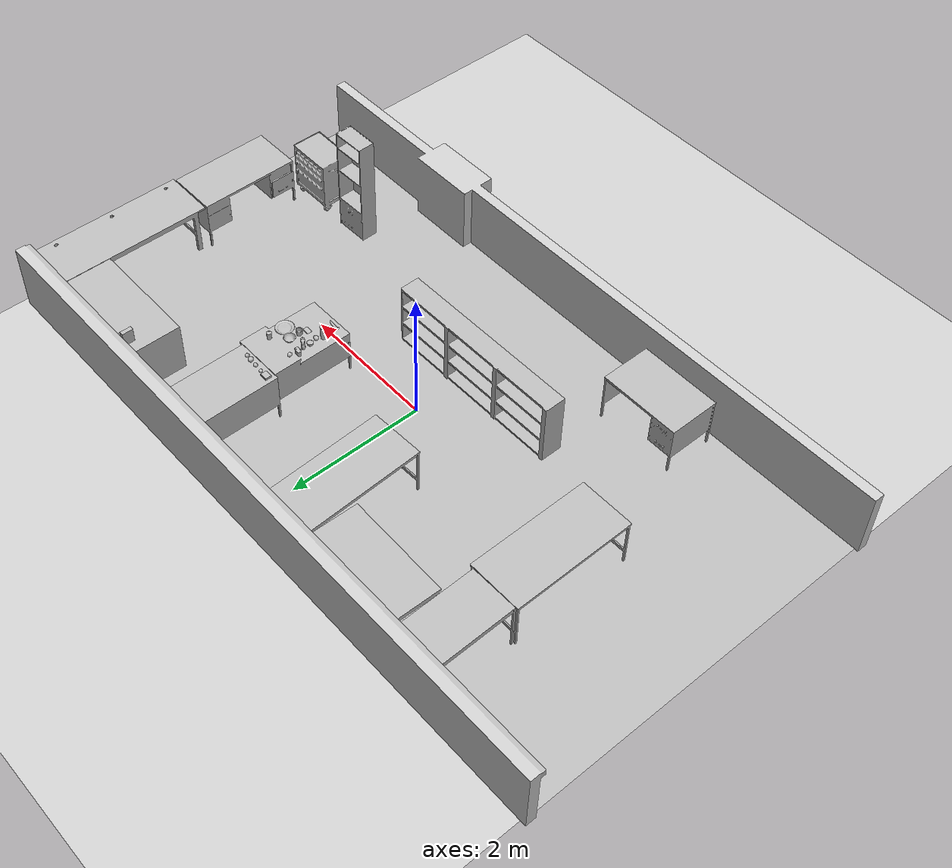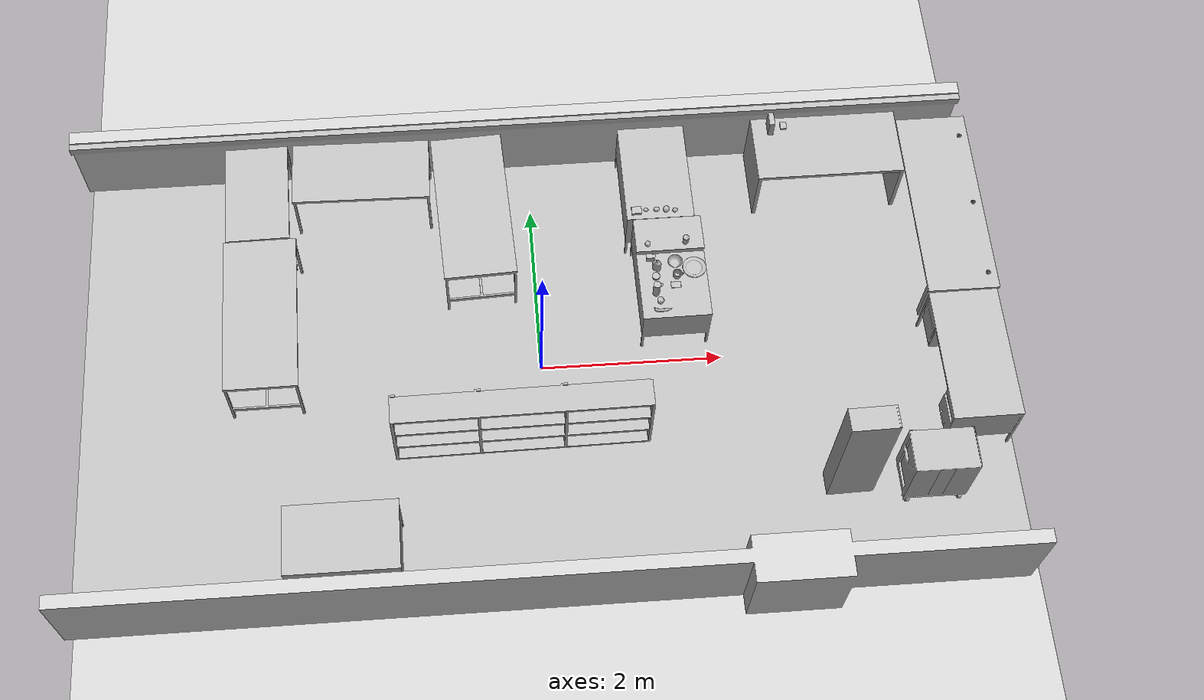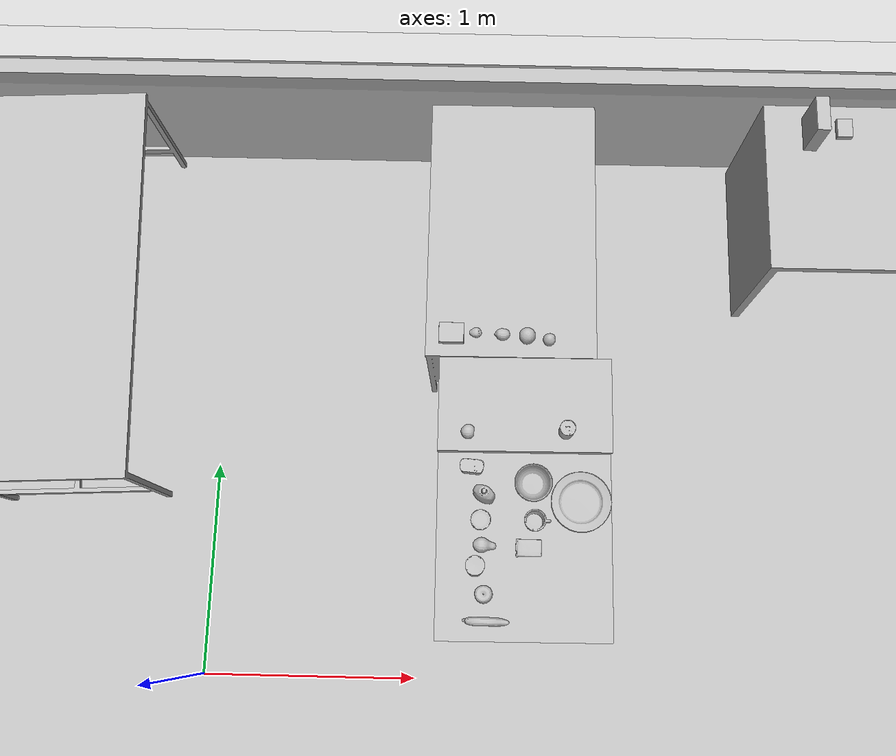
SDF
<sdf version="1.7">
 <world name="default">
  <gravity>0 0 -9.8</gravity>
  <magnetic_field>6e-06 2.3e-05 -4.2e-05</magnetic_field>
  <atmosphere type="adiabatic"/>
  <physics type="ode">
   <max_step_size>0.001</max_step_size>
   <real_time_factor>1</real_time_factor>
   <real_time_update_rate>1000</real_time_update_rate>
  </physics>
  <scene><ambient>0.4 0.4 0.4 1</ambient><background>0.7 0.7 0.7 1</background><shadows>1</shadows></scene>
  <spherical_coordinates>
   <surface_model>EARTH_WGS84</surface_model>
   <latitude_deg>0</latitude_deg>
   <longitude_deg>0</longitude_deg>
   <elevation>0</elevation>
   <heading_deg>0</heading_deg>
  </spherical_coordinates>
  <model name="gplane">
   <link name="body">
    <collision name="gplane_coll">
     <geometry><plane><normal>0 0 1</normal><size>10.075 13.18</size></plane></geometry>
     <surface><contact><ode><kp>1e+06</kp><kd>1</kd></ode></contact></surface>
     <laser_retro>2000</laser_retro>
    </collision>
    <visual name="gplane_vis">
     <geometry><plane><normal>0 0 1</normal><size>10.075 13.18</size></plane></geometry>
     <material>
      <script>
       <uri>model://base_materials/carpet/scripts</uri>
       <uri>model://base_materials/carpet/textures</uri>
       <name>carpet/carpet01</name>
      </script>
     </material>
     <cast_shadows>0</cast_shadows>
    </visual>
    <velocity_decay><linear>0</linear><angular>0</angular></velocity_decay>
   </link>
   <static>1</static>
  </model>
  <model name="Table_01">
   <link name="link_0">
    <inertial>
     <mass>14</mass>
     <inertia>
      <ixx>0.166667</ixx>
      <ixy>0</ixy>
      <ixz>0</ixz>
      <iyy>0.166667</iyy>
      <iyz>0</iyz>
      <izz>0.166667</izz>
     </inertia>
    </inertial>
    <visual name="visual">
     <geometry><mesh><uri>model://BioRoboticsLab/meshes/Table_01.dae</uri><scale>1 1 1</scale></mesh></geometry>
     <material><lighting>1</lighting><shader type="pixel"/></material>
    </visual>
    <collision name="collision">
     <geometry><mesh><uri>model://BioRoboticsLab/meshes/Table_01.dae</uri><scale>1 1 1</scale></mesh></geometry>
     <surface>
      <friction>
       <ode><mu>1</mu><mu2>1</mu2><fdir1>0 0 0</fdir1><slip1>0</slip1><slip2>0</slip2></ode>
       <torsional>
        <coefficient>1</coefficient>
        <patch_radius>0</patch_radius>
        <surface_radius>0</surface_radius>
        <use_patch_radius>1</use_patch_radius>
        <ode><slip>0</slip></ode>
       </torsional>
      </friction>
      <bounce><restitution_coefficient>0</restitution_coefficient><threshold>1e+06</threshold></bounce>
      <contact>
       <collide_without_contact>0</collide_without_contact>
       <collide_without_contact_bitmask>1</collide_without_contact_bitmask>
       <collide_bitmask>1</collide_bitmask>
       <ode>
        <soft_cfm>0</soft_cfm>
        <soft_erp>0.2</soft_erp>
        <kp>1e+13</kp>
        <kd>1</kd>
        <max_vel>0.01</max_vel>
        <min_depth>0</min_depth>
       </ode>
       <bullet>
        <split_impulse>1</split_impulse>
        <split_impulse_penetration_threshold>-0.01</split_impulse_penetration_threshold>
        <soft_cfm>0</soft_cfm>
        <soft_erp>0.2</soft_erp>
        <kp>1e+13</kp>
        <kd>1</kd>
       </bullet>
      </contact>
     </surface>
    </collision>
   </link>
   <static>1</static>
   <pose>4.62119 1.38763 0 0 -0 1.57</pose>
  </model>
  <model name="Table_02">
   <link name="link_0">
    <inertial>
     <mass>15</mass>
     <inertia>
      <ixx>0.166667</ixx>
      <ixy>0</ixy>
      <ixz>0</ixz>
      <iyy>0.166667</iyy>
      <iyz>0</iyz>
      <izz>0.166667</izz>
     </inertia>
    </inertial>
    <visual name="visual">
     <geometry><mesh><uri>model://BioRoboticsLab/meshes/Table_02.dae</uri><scale>1 1 1</scale></mesh></geometry>
     <material><lighting>1</lighting><shader type="pixel"/></material>
    </visual>
    <collision name="collision">
     <geometry><mesh><uri>model://BioRoboticsLab/meshes/Table_02.dae</uri><scale>1 1 1</scale></mesh></geometry>
     <surface>
      <friction>
       <ode><mu>1</mu><mu2>1</mu2><fdir1>0 0 0</fdir1><slip1>0</slip1><slip2>0</slip2></ode>
       <torsional>
        <coefficient>1</coefficient>
        <patch_radius>0</patch_radius>
        <surface_radius>0</surface_radius>
        <use_patch_radius>1</use_patch_radius>
        <ode><slip>0</slip></ode>
       </torsional>
      </friction>
      <bounce><restitution_coefficient>0</restitution_coefficient><threshold>1e+06</threshold></bounce>
      <contact>
       <collide_without_contact>0</collide_without_contact>
       <collide_without_contact_bitmask>1</collide_without_contact_bitmask>
       <collide_bitmask>1</collide_bitmask>
       <ode>
        <soft_cfm>0</soft_cfm>
        <soft_erp>0.2</soft_erp>
        <kp>1e+13</kp>
        <kd>1</kd>
        <max_vel>0.01</max_vel>
        <min_depth>0</min_depth>
       </ode>
       <bullet>
        <split_impulse>1</split_impulse>
        <split_impulse_penetration_threshold>-0.01</split_impulse_penetration_threshold>
        <soft_cfm>0</soft_cfm>
        <soft_erp>0.2</soft_erp>
        <kp>1e+13</kp>
        <kd>1</kd>
       </bullet>
      </contact>
     </surface>
    </collision>
   </link>
   <static>1</static>
   <pose>3.3966 2.2962 0 0 0 -3.14159</pose>
  </model>
  <model name="Table_03">
   <link name="link_0">
    <inertial>
     <mass>8</mass>
     <inertia>
      <ixx>0.166667</ixx>
      <ixy>0</ixy>
      <ixz>0</ixz>
      <iyy>0.166667</iyy>
      <iyz>0</iyz>
      <izz>0.166667</izz>
     </inertia>
    </inertial>
    <visual name="visual">
     <geometry><mesh><uri>model://BioRoboticsLab/meshes/Table_03.dae</uri><scale>1 1 1</scale></mesh></geometry>
     <material><lighting>1</lighting><shader type="pixel"/></material>
    </visual>
    <collision name="collision">
     <geometry><mesh><uri>model://BioRoboticsLab/meshes/Table_03.dae</uri><scale>1 1 1</scale></mesh></geometry>
     <surface>
      <friction>
       <ode><mu>1</mu><mu2>1</mu2><fdir1>0 0 0</fdir1><slip1>0</slip1><slip2>0</slip2></ode>
       <torsional>
        <coefficient>1</coefficient>
        <patch_radius>0</patch_radius>
        <surface_radius>0</surface_radius>
        <use_patch_radius>1</use_patch_radius>
        <ode><slip>0</slip></ode>
       </torsional>
      </friction>
      <bounce><restitution_coefficient>0</restitution_coefficient><threshold>1e+06</threshold></bounce>
      <contact>
       <collide_without_contact>0</collide_without_contact>
       <collide_without_contact_bitmask>1</collide_without_contact_bitmask>
       <collide_bitmask>1</collide_bitmask>
       <ode>
        <soft_cfm>0</soft_cfm>
        <soft_erp>0.2</soft_erp>
        <kp>1e+13</kp>
        <kd>1</kd>
        <max_vel>0.01</max_vel>
        <min_depth>0</min_depth>
       </ode>
       <bullet>
        <split_impulse>1</split_impulse>
        <split_impulse_penetration_threshold>-0.01</split_impulse_penetration_threshold>
        <soft_cfm>0</soft_cfm>
        <soft_erp>0.2</soft_erp>
        <kp>1e+13</kp>
        <kd>1</kd>
       </bullet>
      </contact>
     </surface>
    </collision>
   </link>
   <static>1</static>
   <pose>-0.655137 1.71075 0 0 -0 1.61624</pose>
  </model>
  <model name="Shelf_02">
   <link name="link_0">
    <inertial>
     <mass>12</mass>
     <inertia>
      <ixx>0.166667</ixx>
      <ixy>0</ixy>
      <ixz>0</ixz>
      <iyy>0.166667</iyy>
      <iyz>0</iyz>
      <izz>0.166667</izz>
     </inertia>
    </inertial>
    <visual name="visual">
     <geometry><mesh><uri>model://BioRoboticsLab/meshes/Shelf_02.dae</uri><scale>1 1 1</scale></mesh></geometry>
     <material><lighting>1</lighting><shader type="pixel"/></material>
    </visual>
    <collision name="collision">
     <geometry><mesh><uri>model://BioRoboticsLab/meshes/Shelf_02.dae</uri><scale>1 1 1</scale></mesh></geometry>
     <surface>
      <friction>
       <ode><mu>1</mu><mu2>1</mu2><fdir1>0 0 0</fdir1><slip1>0</slip1><slip2>0</slip2></ode>
       <torsional>
        <coefficient>1</coefficient>
        <patch_radius>0</patch_radius>
        <surface_radius>0</surface_radius>
        <use_patch_radius>1</use_patch_radius>
        <ode><slip>0</slip></ode>
       </torsional>
      </friction>
      <bounce><restitution_coefficient>0</restitution_coefficient><threshold>1e+06</threshold></bounce>
      <contact>
       <collide_without_contact>0</collide_without_contact>
       <collide_without_contact_bitmask>1</collide_without_contact_bitmask>
       <collide_bitmask>1</collide_bitmask>
       <ode>
        <soft_cfm>0</soft_cfm>
        <soft_erp>0.2</soft_erp>
        <kp>1e+13</kp>
        <kd>1</kd>
        <max_vel>0.01</max_vel>
        <min_depth>0</min_depth>
       </ode>
       <bullet>
        <split_impulse>1</split_impulse>
        <split_impulse_penetration_threshold>-0.01</split_impulse_penetration_threshold>
        <soft_cfm>0</soft_cfm>
        <soft_erp>0.2</soft_erp>
        <kp>1e+13</kp>
        <kd>1</kd>
       </bullet>
      </contact>
     </surface>
    </collision>
   </link>
   <static>1</static>
   <pose>3.1815  -1.58084 0 0 -0 0.019976</pose>
  </model>
  <model name="Lab_Mesh">
   <link name="link_0">
    <inertial>
     <mass>100000</mass>
     <inertia>
      <ixx>0.166667</ixx>
      <ixy>0</ixy>
      <ixz>0</ixz>
      <iyy>0.166667</iyy>
      <iyz>0</iyz>
      <izz>0.166667</izz>
     </inertia>
    </inertial>
    <visual name="visual">
     <geometry><mesh><uri>model://BioRoboticsLab/meshes/Lab_Mesh.dae</uri><scale>1 1 1</scale></mesh></geometry>
     <material><lighting>1</lighting><shader type="pixel"/></material>
    </visual>
    <collision name="collision">
     <geometry><mesh><uri>model://BioRoboticsLab/meshes/Lab_Mesh.dae</uri><scale>1 1 1</scale></mesh></geometry>
     <surface>
      <friction>
       <ode><mu>1</mu><mu2>1</mu2><fdir1>0 0 0</fdir1><slip1>0</slip1><slip2>0</slip2></ode>
       <torsional>
        <coefficient>1</coefficient>
        <patch_radius>0</patch_radius>
        <surface_radius>0</surface_radius>
        <use_patch_radius>1</use_patch_radius>
        <ode><slip>0</slip></ode>
       </torsional>
      </friction>
      <bounce><restitution_coefficient>0</restitution_coefficient><threshold>1e+06</threshold></bounce>
      <contact>
       <collide_without_contact>0</collide_without_contact>
       <collide_without_contact_bitmask>1</collide_without_contact_bitmask>
       <collide_bitmask>1</collide_bitmask>
       <ode>
        <soft_cfm>0</soft_cfm>
        <soft_erp>0.2</soft_erp>
        <kp>1e+13</kp>
        <kd>1</kd>
        <max_vel>0.01</max_vel>
        <min_depth>0</min_depth>
       </ode>
       <bullet>
        <split_impulse>1</split_impulse>
        <split_impulse_penetration_threshold>-0.01</split_impulse_penetration_threshold>
        <soft_cfm>0</soft_cfm>
        <soft_erp>0.2</soft_erp>
        <kp>1e+13</kp>
        <kd>1</kd>
       </bullet>
      </contact>
     </surface>
    </collision>
   </link>
   <static>1</static>
   <pose>-0.092622 0.025231 0 0 -0 0</pose>
  </model>
  <model name="Lab_Floor">
   <link name="link_0">
    <inertial>
     <mass>1</mass>
     <inertia>
      <ixx>0.166667</ixx>
      <ixy>0</ixy>
      <ixz>0</ixz>
      <iyy>0.166667</iyy>
      <iyz>0</iyz>
      <izz>0.166667</izz>
     </inertia>
    </inertial>
    <visual name="visual">
     <geometry><mesh><uri>model://BioRoboticsLab/meshes/Lab_Floor.dae</uri><scale>1 1 1</scale></mesh></geometry>
     <material><lighting>1</lighting><shader type="pixel"/></material>
    </visual>
   </link>
   <static>1</static>
   <pose>0 0 0.005 0 -0 0</pose>
  </model>
  <model name="001_chips_can">
   <link name="link_0">
    <inertial>
     <mass>1</mass>
     <inertia>
      <ixx>0.166667</ixx>
      <ixy>0</ixy>
      <ixz>0</ixz>
      <iyy>0.166667</iyy>
      <iyz>0</iyz>
      <izz>0.166667</izz>
     </inertia>
    </inertial>
    <visual name="visual">
     <geometry><mesh><uri>model://YCB_virtual/meshes/001_chips_can.dae</uri><scale>1 1 1</scale></mesh></geometry>
     <material><lighting>1</lighting><shader type="pixel"/></material>
    </visual>
    <collision name="collision">
     <geometry><mesh><uri>model://YCB_virtual/meshes/001_chips_can.dae</uri><scale>1 1 1</scale></mesh></geometry>
     <surface>
      <friction>
       <ode><mu>1</mu><mu2>1</mu2><fdir1>0 0 0</fdir1><slip1>0</slip1><slip2>0</slip2></ode>
       <torsional>
        <coefficient>1</coefficient>
        <patch_radius>0</patch_radius>
        <surface_radius>0</surface_radius>
        <use_patch_radius>1</use_patch_radius>
        <ode><slip>0</slip></ode>
       </torsional>
      </friction>
      <bounce><restitution_coefficient>0</restitution_coefficient><threshold>1e+06</threshold></bounce>
      <contact>
       <collide_without_contact>0</collide_without_contact>
       <collide_without_contact_bitmask>1</collide_without_contact_bitmask>
       <collide_bitmask>1</collide_bitmask>
       <ode>
        <soft_cfm>0</soft_cfm>
        <soft_erp>0.2</soft_erp>
        <kp>1e+13</kp>
        <kd>1</kd>
        <max_vel>0.01</max_vel>
        <min_depth>0</min_depth>
       </ode>
       <bullet>
        <split_impulse>1</split_impulse>
        <split_impulse_penetration_threshold>-0.01</split_impulse_penetration_threshold>
        <soft_cfm>0</soft_cfm>
        <soft_erp>0.2</soft_erp>
        <kp>1e+13</kp>
        <kd>1</kd>
       </bullet>
      </contact>
     </surface>
    </collision>
   </link>
   <static>0</static>
   <pose>1.27967 0.489298 0.77999 1e-06 2e-06 -0.921269</pose>
  </model>
  <model name="003_cracker_box">
   <link name="link_0">
    <inertial>
     <mass>1</mass>
     <inertia>
      <ixx>0.166667</ixx>
      <ixy>0</ixy>
      <ixz>0</ixz>
      <iyy>0.166667</iyy>
      <iyz>0</iyz>
      <izz>0.166667</izz>
     </inertia>
    </inertial>
    <visual name="visual">
     <geometry>
      <mesh><uri>model://YCB_virtual/meshes/003_cracker_box.dae</uri><scale>1 1 1</scale></mesh>
     </geometry>
     <material><lighting>1</lighting><shader type="pixel"/></material>
    </visual>
    <collision name="collision">
     <geometry>
      <mesh><uri>model://YCB_virtual/meshes/003_cracker_box.dae</uri><scale>1 1 1</scale></mesh>
     </geometry>
     <surface>
      <friction>
       <ode><mu>1</mu><mu2>1</mu2><fdir1>0 0 0</fdir1><slip1>0</slip1><slip2>0</slip2></ode>
       <torsional>
        <coefficient>1</coefficient>
        <patch_radius>0</patch_radius>
        <surface_radius>0</surface_radius>
        <use_patch_radius>1</use_patch_radius>
        <ode><slip>0</slip></ode>
       </torsional>
      </friction>
      <bounce><restitution_coefficient>0</restitution_coefficient><threshold>1e+06</threshold></bounce>
      <contact>
       <collide_without_contact>0</collide_without_contact>
       <collide_without_contact_bitmask>1</collide_without_contact_bitmask>
       <collide_bitmask>1</collide_bitmask>
       <ode>
        <soft_cfm>0</soft_cfm>
        <soft_erp>0.2</soft_erp>
        <kp>1e+13</kp>
        <kd>1</kd>
        <max_vel>0.01</max_vel>
        <min_depth>0</min_depth>
       </ode>
       <bullet>
        <split_impulse>1</split_impulse>
        <split_impulse_penetration_threshold>-0.01</split_impulse_penetration_threshold>
        <soft_cfm>0</soft_cfm>
        <soft_erp>0.2</soft_erp>
        <kp>1e+13</kp>
        <kd>1</kd>
       </bullet>
      </contact>
     </surface>
    </collision>
   </link>
   <static>0</static>
   <pose>2.7741 2.47991 0.86 2e-06 -1e-06 8.8e-05</pose>
  </model>
  <model name="005_tomato_soup_can">
   <link name="link_0">
    <inertial>
     <mass>0.31</mass>
     <inertia>
      <ixx>0.166667</ixx>
      <ixy>0</ixy>
      <ixz>0</ixz>
      <iyy>0.166667</iyy>
      <iyz>0</iyz>
      <izz>0.166667</izz>
     </inertia>
    </inertial>
    <visual name="visual">
     <geometry>
      <mesh><uri>model://YCB_virtual/meshes/005_tomato_soup_can.dae</uri><scale>1 1 1</scale></mesh>
     </geometry>
     <material><lighting>1</lighting><shader type="pixel"/></material>
    </visual>
    <collision name="collision">
     <geometry>
      <mesh><uri>model://YCB_virtual/meshes/005_tomato_soup_can.dae</uri><scale>1 1 1</scale></mesh>
     </geometry>
     <surface>
      <friction>
       <ode><mu>1</mu><mu2>1</mu2><fdir1>0 0 0</fdir1><slip1>0</slip1><slip2>0</slip2></ode>
       <torsional>
        <coefficient>1</coefficient>
        <patch_radius>0</patch_radius>
        <surface_radius>0</surface_radius>
        <use_patch_radius>1</use_patch_radius>
        <ode><slip>0</slip></ode>
       </torsional>
      </friction>
      <bounce><restitution_coefficient>0</restitution_coefficient><threshold>1e+06</threshold></bounce>
      <contact>
       <collide_without_contact>0</collide_without_contact>
       <collide_without_contact_bitmask>1</collide_without_contact_bitmask>
       <collide_bitmask>1</collide_bitmask>
       <ode>
        <soft_cfm>0</soft_cfm>
        <soft_erp>0.2</soft_erp>
        <kp>1e+13</kp>
        <kd>1</kd>
        <max_vel>0.01</max_vel>
        <min_depth>0</min_depth>
       </ode>
       <bullet>
        <split_impulse>1</split_impulse>
        <split_impulse_penetration_threshold>-0.01</split_impulse_penetration_threshold>
        <soft_cfm>0</soft_cfm>
        <soft_erp>0.2</soft_erp>
        <kp>1e+13</kp>
        <kd>1</kd>
       </bullet>
      </contact>
     </surface>
    </collision>
   </link>
   <static>0</static>
   <pose>1.65812 1.06628 0.813158 5e-06 -1e-06 -1.22185</pose>
  </model>
  <model name="006_mustard_bottle">
   <link name="link_0">
    <inertial>
     <mass>0.567</mass>
     <inertia>
      <ixx>0.166667</ixx>
      <ixy>0</ixy>
      <ixz>0</ixz>
      <iyy>0.166667</iyy>
      <iyz>0</iyz>
      <izz>0.166667</izz>
     </inertia>
    </inertial>
    <visual name="visual">
     <geometry>
      <mesh><uri>model://YCB_virtual/meshes/006_mustard_bottle.dae</uri><scale>1 1 1</scale></mesh>
     </geometry>
     <material><lighting>1</lighting><shader type="pixel"/></material>
    </visual>
    <collision name="collision">
     <geometry>
      <mesh><uri>model://YCB_virtual/meshes/006_mustard_bottle.dae</uri><scale>1 1 1</scale></mesh>
     </geometry>
     <surface>
      <friction>
       <ode><mu>1</mu><mu2>1</mu2><fdir1>0 0 0</fdir1><slip1>0</slip1><slip2>0</slip2></ode>
       <torsional>
        <coefficient>1</coefficient>
        <patch_radius>0</patch_radius>
        <surface_radius>0</surface_radius>
        <use_patch_radius>1</use_patch_radius>
        <ode><slip>0</slip></ode>
       </torsional>
      </friction>
      <bounce><restitution_coefficient>0</restitution_coefficient><threshold>1e+06</threshold></bounce>
      <contact>
       <collide_without_contact>0</collide_without_contact>
       <collide_without_contact_bitmask>1</collide_without_contact_bitmask>
       <collide_bitmask>1</collide_bitmask>
       <ode>
        <soft_cfm>0</soft_cfm>
        <soft_erp>0.2</soft_erp>
        <kp>1e+13</kp>
        <kd>1</kd>
        <max_vel>0.01</max_vel>
        <min_depth>0</min_depth>
       </ode>
       <bullet>
        <split_impulse>1</split_impulse>
        <split_impulse_penetration_threshold>-0.01</split_impulse_penetration_threshold>
        <soft_cfm>0</soft_cfm>
        <soft_erp>0.2</soft_erp>
        <kp>1e+13</kp>
        <kd>1</kd>
       </bullet>
      </contact>
     </surface>
    </collision>
   </link>
   <static>0</static>
   <pose>1.31148 0.793234 0.762003 -1.7e-05 4e-06 -2.04525</pose>
  </model>
  <model name="007_tuna_fish_can">
   <link name="link_0">
    <inertial>
     <mass>0.113</mass>
     <inertia>
      <ixx>0.166667</ixx>
      <ixy>0</ixy>
      <ixz>0</ixz>
      <iyy>0.166667</iyy>
      <iyz>0</iyz>
      <izz>0.166667</izz>
     </inertia>
    </inertial>
    <visual name="visual">
     <geometry>
      <mesh><uri>model://YCB_virtual/meshes/007_tuna_fish_can.dae</uri><scale>1 1 1</scale></mesh>
     </geometry>
     <material><lighting>1</lighting><shader type="pixel"/></material>
    </visual>
    <collision name="collision">
     <geometry>
      <mesh><uri>model://YCB_virtual/meshes/007_tuna_fish_can.dae</uri><scale>1 1 1</scale></mesh>
     </geometry>
     <surface>
      <friction>
       <ode><mu>1</mu><mu2>1</mu2><fdir1>0 0 0</fdir1><slip1>0</slip1><slip2>0</slip2></ode>
       <torsional>
        <coefficient>1</coefficient>
        <patch_radius>0</patch_radius>
        <surface_radius>0</surface_radius>
        <use_patch_radius>1</use_patch_radius>
        <ode><slip>0</slip></ode>
       </torsional>
      </friction>
      <bounce><restitution_coefficient>0</restitution_coefficient><threshold>1e+06</threshold></bounce>
      <contact>
       <collide_without_contact>0</collide_without_contact>
       <collide_without_contact_bitmask>1</collide_without_contact_bitmask>
       <collide_bitmask>1</collide_bitmask>
       <ode>
        <soft_cfm>0</soft_cfm>
        <soft_erp>0.2</soft_erp>
        <kp>1e+13</kp>
        <kd>1</kd>
        <max_vel>0.01</max_vel>
        <min_depth>0</min_depth>
       </ode>
       <bullet>
        <split_impulse>1</split_impulse>
        <split_impulse_penetration_threshold>-0.01</split_impulse_penetration_threshold>
        <soft_cfm>0</soft_cfm>
        <soft_erp>0.2</soft_erp>
        <kp>1e+13</kp>
        <kd>1</kd>
       </bullet>
      </contact>
     </surface>
    </collision>
   </link>
   <static>0</static>
   <pose>1.29953 0.690057 0.696729 3e-06 -2e-06 -0.986104</pose>
  </model>
  <model name="008_pudding_box">
   <link name="link_0">
    <inertial>
     <mass>0.167</mass>
     <inertia>
      <ixx>0.166667</ixx>
      <ixy>0</ixy>
      <ixz>0</ixz>
      <iyy>0.166667</iyy>
      <iyz>0</iyz>
      <izz>0.166667</izz>
     </inertia>
    </inertial>
    <visual name="visual">
     <geometry>
      <mesh><uri>model://YCB_virtual/meshes/008_pudding_box.dae</uri><scale>1 1 1</scale></mesh>
     </geometry>
     <material><lighting>1</lighting><shader type="pixel"/></material>
    </visual>
    <collision name="collision">
     <geometry>
      <mesh><uri>model://YCB_virtual/meshes/008_pudding_box.dae</uri><scale>1 1 1</scale></mesh>
     </geometry>
     <surface>
      <friction>
       <ode><mu>1</mu><mu2>1</mu2><fdir1>0 0 0</fdir1><slip1>0</slip1><slip2>0</slip2></ode>
       <torsional>
        <coefficient>1</coefficient>
        <patch_radius>0</patch_radius>
        <surface_radius>0</surface_radius>
        <use_patch_radius>1</use_patch_radius>
        <ode><slip>0</slip></ode>
       </torsional>
      </friction>
      <bounce><restitution_coefficient>0</restitution_coefficient><threshold>1e+06</threshold></bounce>
      <contact>
       <collide_without_contact>0</collide_without_contact>
       <collide_without_contact_bitmask>1</collide_without_contact_bitmask>
       <collide_bitmask>1</collide_bitmask>
       <ode>
        <soft_cfm>0</soft_cfm>
        <soft_erp>0.2</soft_erp>
        <kp>1e+13</kp>
        <kd>1</kd>
        <max_vel>0.01</max_vel>
        <min_depth>0</min_depth>
       </ode>
       <bullet>
        <split_impulse>1</split_impulse>
        <split_impulse_penetration_threshold>-0.01</split_impulse_penetration_threshold>
        <soft_cfm>0</soft_cfm>
        <soft_erp>0.2</soft_erp>
        <kp>1e+13</kp>
        <kd>1</kd>
       </bullet>
      </contact>
     </surface>
    </collision>
   </link>
   <static>0</static>
   <pose>1.15528 1.49156 0.777077 0.004784 -0.003859 9.4e-05</pose>
  </model>
  <model name="009_gelatin_box">
   <link name="link_0">
    <inertial>
     <mass>0.09</mass>
     <inertia>
      <ixx>0.166667</ixx>
      <ixy>0</ixy>
      <ixz>0</ixz>
      <iyy>0.166667</iyy>
      <iyz>0</iyz>
      <izz>0.166667</izz>
     </inertia>
    </inertial>
    <visual name="visual">
     <geometry>
      <mesh><uri>model://YCB_virtual/meshes/009_gelatin_box.dae</uri><scale>1 1 1</scale></mesh>
     </geometry>
     <material><lighting>1</lighting><shader type="pixel"/></material>
    </visual>
    <collision name="collision">
     <geometry>
      <mesh><uri>model://YCB_virtual/meshes/009_gelatin_box.dae</uri><scale>1 1 1</scale></mesh>
     </geometry>
     <surface>
      <friction>
       <ode><mu>1</mu><mu2>1</mu2><fdir1>0 0 0</fdir1><slip1>0</slip1><slip2>0</slip2></ode>
       <torsional>
        <coefficient>1</coefficient>
        <patch_radius>0</patch_radius>
        <surface_radius>0</surface_radius>
        <use_patch_radius>1</use_patch_radius>
        <ode><slip>0</slip></ode>
       </torsional>
      </friction>
      <bounce><restitution_coefficient>0</restitution_coefficient><threshold>1e+06</threshold></bounce>
      <contact>
       <collide_without_contact>0</collide_without_contact>
       <collide_without_contact_bitmask>1</collide_without_contact_bitmask>
       <collide_bitmask>1</collide_bitmask>
       <ode>
        <soft_cfm>0</soft_cfm>
        <soft_erp>0.2</soft_erp>
        <kp>1e+13</kp>
        <kd>1</kd>
        <max_vel>0.01</max_vel>
        <min_depth>0</min_depth>
       </ode>
       <bullet>
        <split_impulse>1</split_impulse>
        <split_impulse_penetration_threshold>-0.01</split_impulse_penetration_threshold>
        <soft_cfm>0</soft_cfm>
        <soft_erp>0.2</soft_erp>
        <kp>1e+13</kp>
        <kd>1</kd>
       </bullet>
      </contact>
     </surface>
    </collision>
   </link>
   <static>0</static>
   <pose>2.93226 2.50399 0.769202 -0 0.00419 -3.4e-05</pose>
  </model>
  <model name="010_potted_meat_can">
   <link name="link_0">
    <inertial>
     <mass>0.34</mass>
     <inertia>
      <ixx>0.166667</ixx>
      <ixy>0</ixy>
      <ixz>0</ixz>
      <iyy>0.166667</iyy>
      <iyz>0</iyz>
      <izz>0.166667</izz>
     </inertia>
    </inertial>
    <visual name="visual">
     <geometry>
      <mesh><uri>model://YCB_virtual/meshes/010_potted_meat_can.dae</uri><scale>1 1 1</scale></mesh>
     </geometry>
     <material><lighting>1</lighting><shader type="pixel"/></material>
    </visual>
    <collision name="collision">
     <geometry>
      <mesh><uri>model://YCB_virtual/meshes/010_potted_meat_can.dae</uri><scale>1 1 1</scale></mesh>
     </geometry>
     <surface>
      <friction>
       <ode><mu>1</mu><mu2>1</mu2><fdir1>0 0 0</fdir1><slip1>0</slip1><slip2>0</slip2></ode>
       <torsional>
        <coefficient>1</coefficient>
        <patch_radius>0</patch_radius>
        <surface_radius>0</surface_radius>
        <use_patch_radius>1</use_patch_radius>
        <ode><slip>0</slip></ode>
       </torsional>
      </friction>
      <bounce><restitution_coefficient>0</restitution_coefficient><threshold>1e+06</threshold></bounce>
      <contact>
       <collide_without_contact>0</collide_without_contact>
       <collide_without_contact_bitmask>1</collide_without_contact_bitmask>
       <collide_bitmask>1</collide_bitmask>
       <ode>
        <soft_cfm>0</soft_cfm>
        <soft_erp>0.2</soft_erp>
        <kp>1e+13</kp>
        <kd>1</kd>
        <max_vel>0.01</max_vel>
        <min_depth>0</min_depth>
       </ode>
       <bullet>
        <split_impulse>1</split_impulse>
        <split_impulse_penetration_threshold>-0.01</split_impulse_penetration_threshold>
        <soft_cfm>0</soft_cfm>
        <soft_erp>0.2</soft_erp>
        <kp>1e+13</kp>
        <kd>1</kd>
       </bullet>
      </contact>
     </surface>
    </collision>
   </link>
   <static>0</static>
   <pose>1.25714 0.912689 0.721409 -0 -5e-06 -1.66025</pose>
  </model>
  <model name="011_banana">
   <link name="link_0">
    <inertial>
     <mass>0.2</mass>
     <inertia>
      <ixx>0.166667</ixx>
      <ixy>0</ixy>
      <ixz>0</ixz>
      <iyy>0.166667</iyy>
      <iyz>0</iyz>
      <izz>0.166667</izz>
     </inertia>
    </inertial>
    <visual name="visual">
     <geometry><mesh><uri>model://YCB_virtual/meshes/011_banana.dae</uri><scale>1 1 1</scale></mesh></geometry>
     <material><lighting>1</lighting><shader type="pixel"/></material>
    </visual>
    <collision name="collision">
     <geometry><mesh><uri>model://YCB_virtual/meshes/011_banana.dae</uri><scale>1 1 1</scale></mesh></geometry>
     <surface>
      <friction>
       <ode><mu>1</mu><mu2>1</mu2><fdir1>0 0 0</fdir1><slip1>0</slip1><slip2>0</slip2></ode>
       <torsional>
        <coefficient>1</coefficient>
        <patch_radius>0</patch_radius>
        <surface_radius>0</surface_radius>
        <use_patch_radius>1</use_patch_radius>
        <ode><slip>0</slip></ode>
       </torsional>
      </friction>
      <bounce><restitution_coefficient>0</restitution_coefficient><threshold>1e+06</threshold></bounce>
      <contact>
       <collide_without_contact>0</collide_without_contact>
       <collide_without_contact_bitmask>1</collide_without_contact_bitmask>
       <collide_bitmask>1</collide_bitmask>
       <ode>
        <soft_cfm>0</soft_cfm>
        <soft_erp>0.2</soft_erp>
        <kp>1e+13</kp>
        <kd>1</kd>
        <max_vel>0.01</max_vel>
        <min_depth>0</min_depth>
       </ode>
       <bullet>
        <split_impulse>1</split_impulse>
        <split_impulse_penetration_threshold>-0.01</split_impulse_penetration_threshold>
        <soft_cfm>0</soft_cfm>
        <soft_erp>0.2</soft_erp>
        <kp>1e+13</kp>
        <kd>1</kd>
       </bullet>
      </contact>
     </surface>
    </collision>
   </link>
   <static>0</static>
   <pose>1.32577 0.268796 0.709151 2.49983 -1.4744 -0.943589</pose>
  </model>
  <model name="012_strawberry">
   <link name="link_0">
    <inertial>
     <mass>0.01</mass>
     <inertia>
      <ixx>0.166667</ixx>
      <ixy>0</ixy>
      <ixz>0</ixz>
      <iyy>0.166667</iyy>
      <iyz>0</iyz>
      <izz>0.166667</izz>
     </inertia>
    </inertial>
    <visual name="visual">
     <geometry><mesh><uri>model://YCB_virtual/meshes/012_strawberry.dae</uri><scale>1 1 1</scale></mesh></geometry>
     <material><lighting>1</lighting><shader type="pixel"/></material>
    </visual>
    <collision name="collision">
     <geometry><mesh><uri>model://YCB_virtual/meshes/012_strawberry.dae</uri><scale>1 1 1</scale></mesh></geometry>
     <surface>
      <friction>
       <ode><mu>1</mu><mu2>1</mu2><fdir1>0 0 0</fdir1><slip1>0</slip1><slip2>0</slip2></ode>
       <torsional>
        <coefficient>1</coefficient>
        <patch_radius>0</patch_radius>
        <surface_radius>0</surface_radius>
        <use_patch_radius>1</use_patch_radius>
        <ode><slip>0</slip></ode>
       </torsional>
      </friction>
      <bounce><restitution_coefficient>0</restitution_coefficient><threshold>1e+06</threshold></bounce>
      <contact>
       <collide_without_contact>0</collide_without_contact>
       <collide_without_contact_bitmask>1</collide_without_contact_bitmask>
       <collide_bitmask>1</collide_bitmask>
       <ode>
        <soft_cfm>0</soft_cfm>
        <soft_erp>0.2</soft_erp>
        <kp>1e+13</kp>
        <kd>1</kd>
        <max_vel>0.01</max_vel>
        <min_depth>0</min_depth>
       </ode>
       <bullet>
        <split_impulse>1</split_impulse>
        <split_impulse_penetration_threshold>-0.01</split_impulse_penetration_threshold>
        <soft_cfm>0</soft_cfm>
        <soft_erp>0.2</soft_erp>
        <kp>1e+13</kp>
        <kd>1</kd>
       </bullet>
      </contact>
     </surface>
    </collision>
   </link>
   <static>0</static>
   <pose>1.26453 1.49463 0.780731 0.102856 -0.02475 -0.002407</pose>
  </model>
  <model name="013_apple">
   <link name="link_0">
    <inertial>
     <mass>0.15</mass>
     <inertia>
      <ixx>0.166667</ixx>
      <ixy>0</ixy>
      <ixz>0</ixz>
      <iyy>0.166667</iyy>
      <iyz>0</iyz>
      <izz>0.166667</izz>
     </inertia>
    </inertial>
    <visual name="visual">
     <geometry><mesh><uri>model://YCB_virtual/meshes/013_apple.dae</uri><scale>1 1 1</scale></mesh></geometry>
     <material><lighting>1</lighting><shader type="pixel"/></material>
    </visual>
    <collision name="collision">
     <geometry><mesh><uri>model://YCB_virtual/meshes/013_apple.dae</uri><scale>1 1 1</scale></mesh></geometry>
     <surface>
      <friction>
       <ode><mu>1</mu><mu2>1</mu2><fdir1>0 0 0</fdir1><slip1>0</slip1><slip2>0</slip2></ode>
       <torsional>
        <coefficient>1</coefficient>
        <patch_radius>0</patch_radius>
        <surface_radius>0</surface_radius>
        <use_patch_radius>1</use_patch_radius>
        <ode><slip>0</slip></ode>
       </torsional>
      </friction>
      <bounce><restitution_coefficient>0</restitution_coefficient><threshold>1e+06</threshold></bounce>
      <contact>
       <collide_without_contact>0</collide_without_contact>
       <collide_without_contact_bitmask>1</collide_without_contact_bitmask>
       <collide_bitmask>1</collide_bitmask>
       <ode>
        <soft_cfm>0</soft_cfm>
        <soft_erp>0.2</soft_erp>
        <kp>1e+13</kp>
        <kd>1</kd>
        <max_vel>0.01</max_vel>
        <min_depth>0</min_depth>
       </ode>
       <bullet>
        <split_impulse>1</split_impulse>
        <split_impulse_penetration_threshold>-0.01</split_impulse_penetration_threshold>
        <soft_cfm>0</soft_cfm>
        <soft_erp>0.2</soft_erp>
        <kp>1e+13</kp>
        <kd>1</kd>
       </bullet>
      </contact>
     </surface>
    </collision>
   </link>
   <static>0</static>
   <pose>1.31777 0.378946 0.716823 -0.008413 0.005372 0.000368</pose>
  </model>
  <model name="014_lemon">
   <link name="link_0">
    <inertial>
     <mass>0.1</mass>
     <inertia>
      <ixx>0.166667</ixx>
      <ixy>0</ixy>
      <ixz>0</ixz>
      <iyy>0.166667</iyy>
      <iyz>0</iyz>
      <izz>0.166667</izz>
     </inertia>
    </inertial>
    <visual name="visual">
     <geometry><mesh><uri>model://YCB_virtual/meshes/014_lemon.dae</uri><scale>1 1 1</scale></mesh></geometry>
     <material><lighting>1</lighting><shader type="pixel"/></material>
    </visual>
    <collision name="collision">
     <geometry><mesh><uri>model://YCB_virtual/meshes/014_lemon.dae</uri><scale>1 1 1</scale></mesh></geometry>
     <surface>
      <friction>
       <ode><mu>1</mu><mu2>1</mu2><fdir1>0 0 0</fdir1><slip1>0</slip1><slip2>0</slip2></ode>
       <torsional>
        <coefficient>1</coefficient>
        <patch_radius>0</patch_radius>
        <surface_radius>0</surface_radius>
        <use_patch_radius>1</use_patch_radius>
        <ode><slip>0</slip></ode>
       </torsional>
      </friction>
      <bounce><restitution_coefficient>0</restitution_coefficient><threshold>1e+06</threshold></bounce>
      <contact>
       <collide_without_contact>0</collide_without_contact>
       <collide_without_contact_bitmask>1</collide_without_contact_bitmask>
       <collide_bitmask>1</collide_bitmask>
       <ode>
        <soft_cfm>0</soft_cfm>
        <soft_erp>0.2</soft_erp>
        <kp>1e+13</kp>
        <kd>1</kd>
        <max_vel>0.01</max_vel>
        <min_depth>0</min_depth>
       </ode>
       <bullet>
        <split_impulse>1</split_impulse>
        <split_impulse_penetration_threshold>-0.01</split_impulse_penetration_threshold>
        <soft_cfm>0</soft_cfm>
        <soft_erp>0.2</soft_erp>
        <kp>1e+13</kp>
        <kd>1</kd>
       </bullet>
      </contact>
     </surface>
    </collision>
   </link>
   <static>0</static>
   <pose>1.37886 1.48752 0.78598 0.095457 0.089969 0.003766</pose>
  </model>
  <model name="015_peach">
   <link name="link_0">
    <inertial>
     <mass>0.12</mass>
     <inertia>
      <ixx>0.166667</ixx>
      <ixy>0</ixy>
      <ixz>0</ixz>
      <iyy>0.166667</iyy>
      <iyz>0</iyz>
      <izz>0.166667</izz>
     </inertia>
    </inertial>
    <visual name="visual">
     <geometry><mesh><uri>model://YCB_virtual/meshes/015_peach.dae</uri><scale>1 1 1</scale></mesh></geometry>
     <material><lighting>1</lighting><shader type="pixel"/></material>
    </visual>
    <collision name="collision">
     <geometry><mesh><uri>model://YCB_virtual/meshes/015_peach.dae</uri><scale>1 1 1</scale></mesh></geometry>
     <surface>
      <friction>
       <ode><mu>1</mu><mu2>1</mu2><fdir1>0 0 0</fdir1><slip1>0</slip1><slip2>0</slip2></ode>
       <torsional>
        <coefficient>1</coefficient>
        <patch_radius>0</patch_radius>
        <surface_radius>0</surface_radius>
        <use_patch_radius>1</use_patch_radius>
        <ode><slip>0</slip></ode>
       </torsional>
      </friction>
      <bounce><restitution_coefficient>0</restitution_coefficient><threshold>1e+06</threshold></bounce>
      <contact>
       <collide_without_contact>0</collide_without_contact>
       <collide_without_contact_bitmask>1</collide_without_contact_bitmask>
       <collide_bitmask>1</collide_bitmask>
       <ode>
        <soft_cfm>0</soft_cfm>
        <soft_erp>0.2</soft_erp>
        <kp>1e+13</kp>
        <kd>1</kd>
        <max_vel>0.01</max_vel>
        <min_depth>0</min_depth>
       </ode>
       <bullet>
        <split_impulse>1</split_impulse>
        <split_impulse_penetration_threshold>-0.01</split_impulse_penetration_threshold>
        <soft_cfm>0</soft_cfm>
        <soft_erp>0.2</soft_erp>
        <kp>1e+13</kp>
        <kd>1</kd>
       </bullet>
      </contact>
     </surface>
    </collision>
   </link>
   <static>0</static>
   <pose>1.2384 1.05482 0.788496 0.021421 -0.087371 8.1e-05</pose>
  </model>
  <model name="016_pear">
   <link name="link_0">
    <inertial>
     <mass>0.08</mass>
     <inertia>
      <ixx>0.166667</ixx>
      <ixy>0</ixy>
      <ixz>0</ixz>
      <iyy>0.166667</iyy>
      <iyz>0</iyz>
      <izz>0.166667</izz>
     </inertia>
    </inertial>
    <visual name="visual">
     <geometry><mesh><uri>model://YCB_virtual/meshes/016_pear.dae</uri><scale>1 1 1</scale></mesh></geometry>
     <material><lighting>1</lighting><shader type="pixel"/></material>
    </visual>
    <collision name="collision">
     <geometry><mesh><uri>model://YCB_virtual/meshes/016_pear.dae</uri><scale>1 1 1</scale></mesh></geometry>
     <surface>
      <friction>
       <ode><mu>1</mu><mu2>1</mu2><fdir1>0 0 0</fdir1><slip1>0</slip1><slip2>0</slip2></ode>
       <torsional>
        <coefficient>1</coefficient>
        <patch_radius>0</patch_radius>
        <surface_radius>0</surface_radius>
        <use_patch_radius>1</use_patch_radius>
        <ode><slip>0</slip></ode>
       </torsional>
      </friction>
      <bounce><restitution_coefficient>0</restitution_coefficient><threshold>1e+06</threshold></bounce>
      <contact>
       <collide_without_contact>0</collide_without_contact>
       <collide_without_contact_bitmask>1</collide_without_contact_bitmask>
       <collide_bitmask>1</collide_bitmask>
       <ode>
        <soft_cfm>0</soft_cfm>
        <soft_erp>0.2</soft_erp>
        <kp>1e+13</kp>
        <kd>1</kd>
        <max_vel>0.01</max_vel>
        <min_depth>0</min_depth>
       </ode>
       <bullet>
        <split_impulse>1</split_impulse>
        <split_impulse_penetration_threshold>-0.01</split_impulse_penetration_threshold>
        <soft_cfm>0</soft_cfm>
        <soft_erp>0.2</soft_erp>
        <kp>1e+13</kp>
        <kd>1</kd>
       </bullet>
      </contact>
     </surface>
    </collision>
   </link>
   <static>0</static>
   <pose>1.31283 0.583258 0.709437 -0.083304 0.301562 -0.047994</pose>
  </model>
  <model name="017_orange">
   <link name="link_0">
    <inertial>
     <mass>0.25</mass>
     <inertia>
      <ixx>0.166667</ixx>
      <ixy>0</ixy>
      <ixz>0</ixz>
      <iyy>0.166667</iyy>
      <iyz>0</iyz>
      <izz>0.166667</izz>
     </inertia>
    </inertial>
    <visual name="visual">
     <geometry><mesh><uri>model://YCB_virtual/meshes/017_orange.dae</uri><scale>1 1 1</scale></mesh></geometry>
     <material><lighting>1</lighting><shader type="pixel"/></material>
    </visual>
    <collision name="collision">
     <geometry><mesh><uri>model://YCB_virtual/meshes/017_orange.dae</uri><scale>1 1 1</scale></mesh></geometry>
     <surface>
      <friction>
       <ode><mu>1</mu><mu2>1</mu2><fdir1>0 0 0</fdir1><slip1>0</slip1><slip2>0</slip2></ode>
       <torsional>
        <coefficient>1</coefficient>
        <patch_radius>0</patch_radius>
        <surface_radius>0</surface_radius>
        <use_patch_radius>1</use_patch_radius>
        <ode><slip>0</slip></ode>
       </torsional>
      </friction>
      <bounce><restitution_coefficient>0</restitution_coefficient><threshold>1e+06</threshold></bounce>
      <contact>
       <collide_without_contact>0</collide_without_contact>
       <collide_without_contact_bitmask>1</collide_without_contact_bitmask>
       <collide_bitmask>1</collide_bitmask>
       <ode>
        <soft_cfm>0</soft_cfm>
        <soft_erp>0.2</soft_erp>
        <kp>1e+13</kp>
        <kd>1</kd>
        <max_vel>0.01</max_vel>
        <min_depth>0</min_depth>
       </ode>
       <bullet>
        <split_impulse>1</split_impulse>
        <split_impulse_penetration_threshold>-0.01</split_impulse_penetration_threshold>
        <soft_cfm>0</soft_cfm>
        <soft_erp>0.2</soft_erp>
        <kp>1e+13</kp>
        <kd>1</kd>
       </bullet>
      </contact>
     </surface>
    </collision>
   </link>
   <static>0</static>
   <pose>1.48638 1.48128 0.793781 0.006122 0.022557 -3.4e-05</pose>
  </model>
  <model name="018_plum">
   <link name="link_0">
    <inertial>
     <mass>0.08</mass>
     <inertia>
      <ixx>0.166667</ixx>
      <ixy>0</ixy>
      <ixz>0</ixz>
      <iyy>0.166667</iyy>
      <iyz>0</iyz>
      <izz>0.166667</izz>
     </inertia>
    </inertial>
    <visual name="visual">
     <geometry><mesh><uri>model://YCB_virtual/meshes/018_plum.dae</uri><scale>1 1 1</scale></mesh></geometry>
     <material><lighting>1</lighting><shader type="pixel"/></material>
    </visual>
    <collision name="collision">
     <geometry><mesh><uri>model://YCB_virtual/meshes/018_plum.dae</uri><scale>1 1 1</scale></mesh></geometry>
     <surface>
      <friction>
       <ode><mu>1</mu><mu2>1</mu2><fdir1>0 0 0</fdir1><slip1>0</slip1><slip2>0</slip2></ode>
       <torsional>
        <coefficient>1</coefficient>
        <patch_radius>0</patch_radius>
        <surface_radius>0</surface_radius>
        <use_patch_radius>1</use_patch_radius>
        <ode><slip>0</slip></ode>
       </torsional>
      </friction>
      <bounce><restitution_coefficient>0</restitution_coefficient><threshold>1e+06</threshold></bounce>
      <contact>
       <collide_without_contact>0</collide_without_contact>
       <collide_without_contact_bitmask>1</collide_without_contact_bitmask>
       <collide_bitmask>1</collide_bitmask>
       <ode>
        <soft_cfm>0</soft_cfm>
        <soft_erp>0.2</soft_erp>
        <kp>1e+13</kp>
        <kd>1</kd>
        <max_vel>0.01</max_vel>
        <min_depth>0</min_depth>
       </ode>
       <bullet>
        <split_impulse>1</split_impulse>
        <split_impulse_penetration_threshold>-0.01</split_impulse_penetration_threshold>
        <soft_cfm>0</soft_cfm>
        <soft_erp>0.2</soft_erp>
        <kp>1e+13</kp>
        <kd>1</kd>
       </bullet>
      </contact>
     </surface>
    </collision>
   </link>
   <static>0</static>
   <pose>1.58296 1.46964 0.783689 0.00579 -0.027533 7.1e-05</pose>
  </model>
  <model name="024_bowl">
   <link name="link_0">
    <inertial>
     <mass>0.4</mass>
     <inertia>
      <ixx>0.166667</ixx>
      <ixy>0</ixy>
      <ixz>0</ixz>
      <iyy>0.166667</iyy>
      <iyz>0</iyz>
      <izz>0.166667</izz>
     </inertia>
    </inertial>
    <visual name="visual">
     <geometry><mesh><uri>model://YCB_virtual/meshes/024_bowl.dae</uri><scale>1 1 1</scale></mesh></geometry>
     <material><lighting>1</lighting><shader type="pixel"/></material>
    </visual>
    <collision name="collision">
     <geometry><mesh><uri>model://YCB_virtual/meshes/024_bowl.dae</uri><scale>1 1 1</scale></mesh></geometry>
     <surface>
      <friction>
       <ode><mu>1</mu><mu2>1</mu2><fdir1>0 0 0</fdir1><slip1>0</slip1><slip2>0</slip2></ode>
       <torsional>
        <coefficient>1</coefficient>
        <patch_radius>0</patch_radius>
        <surface_radius>0</surface_radius>
        <use_patch_radius>1</use_patch_radius>
        <ode><slip>0</slip></ode>
       </torsional>
      </friction>
      <bounce><restitution_coefficient>0</restitution_coefficient><threshold>1e+06</threshold></bounce>
      <contact>
       <collide_without_contact>0</collide_without_contact>
       <collide_without_contact_bitmask>1</collide_without_contact_bitmask>
       <collide_bitmask>1</collide_bitmask>
       <ode>
        <soft_cfm>0</soft_cfm>
        <soft_erp>0.2</soft_erp>
        <kp>1e+13</kp>
        <kd>1</kd>
        <max_vel>0.01</max_vel>
        <min_depth>0</min_depth>
       </ode>
       <bullet>
        <split_impulse>1</split_impulse>
        <split_impulse_penetration_threshold>-0.01</split_impulse_penetration_threshold>
        <soft_cfm>0</soft_cfm>
        <soft_erp>0.2</soft_erp>
        <kp>1e+13</kp>
        <kd>1</kd>
       </bullet>
      </contact>
     </surface>
    </collision>
   </link>
   <static>0</static>
   <pose>1.52195 0.84998 0.704982 1e-06 -1e-06 -0.000366</pose>
  </model>
  <model name="025_mug">
   <link name="link_0">
    <inertial>
     <mass>0.3</mass>
     <inertia>
      <ixx>0.166667</ixx>
      <ixy>0</ixy>
      <ixz>0</ixz>
      <iyy>0.166667</iyy>
      <iyz>0</iyz>
      <izz>0.166667</izz>
     </inertia>
    </inertial>
    <visual name="visual">
     <geometry><mesh><uri>model://YCB_virtual/meshes/025_mug.dae</uri><scale>1 1 1</scale></mesh></geometry>
     <material><lighting>1</lighting><shader type="pixel"/></material>
    </visual>
    <collision name="collision">
     <geometry><mesh><uri>model://YCB_virtual/meshes/025_mug.dae</uri><scale>1 1 1</scale></mesh></geometry>
     <surface>
      <friction>
       <ode><mu>1</mu><mu2>1</mu2><fdir1>0 0 0</fdir1><slip1>0</slip1><slip2>0</slip2></ode>
       <torsional>
        <coefficient>1</coefficient>
        <patch_radius>0</patch_radius>
        <surface_radius>0</surface_radius>
        <use_patch_radius>1</use_patch_radius>
        <ode><slip>0</slip></ode>
       </torsional>
      </friction>
      <bounce><restitution_coefficient>0</restitution_coefficient><threshold>1e+06</threshold></bounce>
      <contact>
       <collide_without_contact>0</collide_without_contact>
       <collide_without_contact_bitmask>1</collide_without_contact_bitmask>
       <collide_bitmask>1</collide_bitmask>
       <ode>
        <soft_cfm>0</soft_cfm>
        <soft_erp>0.2</soft_erp>
        <kp>1e+13</kp>
        <kd>1</kd>
        <max_vel>0.01</max_vel>
        <min_depth>0</min_depth>
       </ode>
       <bullet>
        <split_impulse>1</split_impulse>
        <split_impulse_penetration_threshold>-0.01</split_impulse_penetration_threshold>
        <soft_cfm>0</soft_cfm>
        <soft_erp>0.2</soft_erp>
        <kp>1e+13</kp>
        <kd>1</kd>
       </bullet>
      </contact>
     </surface>
    </collision>
   </link>
   <static>0</static>
   <pose>1.52915 0.687979 0.71727 0 -2e-06 0.000215</pose>
  </model>
  <model name="026_sponge">
   <link name="link_0">
    <inertial>
     <mass>0.01</mass>
     <inertia>
      <ixx>0.166667</ixx>
      <ixy>0</ixy>
      <ixz>0</ixz>
      <iyy>0.166667</iyy>
      <iyz>0</iyz>
      <izz>0.166667</izz>
     </inertia>
    </inertial>
    <visual name="visual">
     <geometry><mesh><uri>model://YCB_virtual/meshes/026_sponge.dae</uri><scale>1 1 1</scale></mesh></geometry>
     <material><lighting>1</lighting><shader type="pixel"/></material>
    </visual>
    <collision name="collision">
     <geometry><mesh><uri>model://YCB_virtual/meshes/026_sponge.dae</uri><scale>1 1 1</scale></mesh></geometry>
     <surface>
      <friction>
       <ode><mu>1</mu><mu2>1</mu2><fdir1>0 0 0</fdir1><slip1>0</slip1><slip2>0</slip2></ode>
       <torsional>
        <coefficient>1</coefficient>
        <patch_radius>0</patch_radius>
        <surface_radius>0</surface_radius>
        <use_patch_radius>1</use_patch_radius>
        <ode><slip>0</slip></ode>
       </torsional>
      </friction>
      <bounce><restitution_coefficient>0</restitution_coefficient><threshold>1e+06</threshold></bounce>
      <contact>
       <collide_without_contact>0</collide_without_contact>
       <collide_without_contact_bitmask>1</collide_without_contact_bitmask>
       <collide_bitmask>1</collide_bitmask>
       <ode>
        <soft_cfm>0</soft_cfm>
        <soft_erp>0.2</soft_erp>
        <kp>1e+13</kp>
        <kd>1</kd>
        <max_vel>0.01</max_vel>
        <min_depth>0</min_depth>
       </ode>
       <bullet>
        <split_impulse>1</split_impulse>
        <split_impulse_penetration_threshold>-0.01</split_impulse_penetration_threshold>
        <soft_cfm>0</soft_cfm>
        <soft_erp>0.2</soft_erp>
        <kp>1e+13</kp>
        <kd>1</kd>
       </bullet>
      </contact>
     </surface>
    </collision>
   </link>
   <static>0</static>
   <pose>1.50629 0.576854 0.688494 0.009334 0.000884 1.56521</pose>
  </model>
  <model name="029_plate">
   <link name="link_0">
    <inertial>
     <mass>0.25</mass>
     <inertia>
      <ixx>0.166667</ixx>
      <ixy>0</ixy>
      <ixz>0</ixz>
      <iyy>0.166667</iyy>
      <iyz>0</iyz>
      <izz>0.166667</izz>
     </inertia>
    </inertial>
    <visual name="visual">
     <geometry><mesh><uri>model://YCB_virtual/meshes/029_plate.dae</uri><scale>1 1 1</scale></mesh></geometry>
     <material><lighting>1</lighting><shader type="pixel"/></material>
    </visual>
    <collision name="collision">
     <geometry><mesh><uri>model://YCB_virtual/meshes/029_plate.dae</uri><scale>1 1 1</scale></mesh></geometry>
     <surface>
      <friction>
       <ode><mu>1</mu><mu2>1</mu2><fdir1>0 0 0</fdir1><slip1>0</slip1><slip2>0</slip2></ode>
       <torsional>
        <coefficient>1</coefficient>
        <patch_radius>0</patch_radius>
        <surface_radius>0</surface_radius>
        <use_patch_radius>1</use_patch_radius>
        <ode><slip>0</slip></ode>
       </torsional>
      </friction>
      <bounce><restitution_coefficient>0</restitution_coefficient><threshold>1e+06</threshold></bounce>
      <contact>
       <collide_without_contact>0</collide_without_contact>
       <collide_without_contact_bitmask>1</collide_without_contact_bitmask>
       <collide_bitmask>1</collide_bitmask>
       <ode>
        <soft_cfm>0</soft_cfm>
        <soft_erp>0.2</soft_erp>
        <kp>1e+13</kp>
        <kd>1</kd>
        <max_vel>0.01</max_vel>
        <min_depth>0</min_depth>
       </ode>
       <bullet>
        <split_impulse>1</split_impulse>
        <split_impulse_penetration_threshold>-0.01</split_impulse_penetration_threshold>
        <soft_cfm>0</soft_cfm>
        <soft_erp>0.2</soft_erp>
        <kp>1e+13</kp>
        <kd>1</kd>
       </bullet>
      </contact>
     </surface>
    </collision>
   </link>
   <static>0</static>
   <pose>1.72819 0.775064 0.690992 1e-06 3e-06 -3.6e-05</pose>
  </model>
  <light name="inner_point_white1" type="point">
   <pose>4 5 4 0 -0 0</pose>
   <diffuse>0.2 0.2 0.2 1</diffuse>
   <specular>0.1 0.1 0.1 1</specular>
   <attenuation>
    <range>20</range>
    <linear>0.1</linear>
    <constant>0.2</constant>
    <quadratic>0</quadratic>
   </attenuation>
   <cast_shadows>0</cast_shadows>
   <direction>0 0 -1</direction>
   <spot><inner_angle>0</inner_angle><outer_angle>0</outer_angle><falloff>0</falloff></spot>
  </light>
  <light name="inner_point_white2" type="point">
   <pose>4 10 4 0 -0 0</pose>
   <diffuse>0.2 0.2 0.2 1</diffuse>
   <specular>0.1 0.1 0.1 1</specular>
   <attenuation>
    <range>20</range>
    <linear>0.1</linear>
    <constant>0.2</constant>
    <quadratic>0</quadratic>
   </attenuation>
   <cast_shadows>0</cast_shadows>
   <direction>0 0 -1</direction>
   <spot><inner_angle>0</inner_angle><outer_angle>0</outer_angle><falloff>0</falloff></spot>
  </light>
  <light name="inner_point_white3" type="point">
   <pose>8 5 4 0 -0 0</pose>
   <diffuse>0.2 0.2 0.2 1</diffuse>
   <specular>0.1 0.1 0.1 1</specular>
   <attenuation>
    <range>20</range>
    <linear>0.1</linear>
    <constant>0.2</constant>
    <quadratic>0</quadratic>
   </attenuation>
   <cast_shadows>0</cast_shadows>
   <direction>0 0 -1</direction>
   <spot><inner_angle>0</inner_angle><outer_angle>0</outer_angle><falloff>0</falloff></spot>
  </light>
  <light name="inner_point_white4" type="point">
   <pose>8 10 4 0 -0 0</pose>
   <diffuse>0.2 0.2 0.2 1</diffuse>
   <specular>0.1 0.1 0.1 1</specular>
   <attenuation>
    <range>20</range>
    <linear>0.1</linear>
    <constant>0.2</constant>
    <quadratic>0</quadratic>
   </attenuation>
   <cast_shadows>0</cast_shadows>
   <direction>0 0 -1</direction>
   <spot><inner_angle>0</inner_angle><outer_angle>0</outer_angle><falloff>0</falloff></spot>
  </light>
  <light name="inner_point_white5" type="point">
   <pose>4 5 4 0 -0 0</pose>
   <diffuse>0.2 0.2 0.2 1</diffuse>
   <specular>0.1 0.1 0.1 1</specular>
   <attenuation>
    <range>20</range>
    <linear>0.1</linear>
    <constant>0.2</constant>
    <quadratic>0</quadratic>
   </attenuation>
   <cast_shadows>0</cast_shadows>
   <direction>0 0 -1</direction>
   <spot><inner_angle>0</inner_angle><outer_angle>0</outer_angle><falloff>0</falloff></spot>
  </light>
  <light name="inner_point_white6" type="point">
   <pose>4 10 4 0 -0 0</pose>
   <diffuse>0.2 0.2 0.2 1</diffuse>
   <specular>0.1 0.1 0.1 1</specular>
   <attenuation>
    <range>20</range>
    <linear>0.1</linear>
    <constant>0.2</constant>
    <quadratic>0</quadratic>
   </attenuation>
   <cast_shadows>0</cast_shadows>
   <direction>0 0 -1</direction>
   <spot><inner_angle>0</inner_angle><outer_angle>0</outer_angle><falloff>0</falloff></spot>
  </light>
  <light name="inner_point_white7" type="point">
   <pose>8 5 4 0 -0 0</pose>
   <diffuse>0.2 0.2 0.2 1</diffuse>
   <specular>0.1 0.1 0.1 1</specular>
   <attenuation>
    <range>20</range>
    <linear>0.1</linear>
    <constant>0.2</constant>
    <quadratic>0</quadratic>
   </attenuation>
   <cast_shadows>0</cast_shadows>
   <direction>0 0 -1</direction>
   <spot><inner_angle>0</inner_angle><outer_angle>0</outer_angle><falloff>0</falloff></spot>
  </light>
  <light name="inner_point_white8" type="point">
   <pose>8 10 4 0 -0 0</pose>
   <diffuse>0.2 0.2 0.2 1</diffuse>
   <specular>0.1 0.1 0.1 1</specular>
   <attenuation>
    <range>20</range>
    <linear>0.1</linear>
    <constant>0.2</constant>
    <quadratic>0</quadratic>
   </attenuation>
   <cast_shadows>0</cast_shadows>
   <direction>0 0 -1</direction>
   <spot><inner_angle>0</inner_angle><outer_angle>0</outer_angle><falloff>0</falloff></spot>
  </light>
  <model name="Table_04">
   <link name="link_0">
    <inertial>
     <mass>8</mass>
     <inertia>
      <ixx>0.166667</ixx>
      <ixy>0</ixy>
      <ixz>0</ixz>
      <iyy>0.166667</iyy>
      <iyz>0</iyz>
      <izz>0.166667</izz>
     </inertia>
    </inertial>
    <visual name="visual">
     <geometry><mesh><uri>model://BioRoboticsLab/meshes/Table_04.dae</uri><scale>1 1 1</scale></mesh></geometry>
     <material><lighting>1</lighting><shader type="pixel"/></material>
    </visual>
    <collision name="collision">
     <geometry><mesh><uri>model://BioRoboticsLab/meshes/Table_04.dae</uri><scale>1 1 1</scale></mesh></geometry>
     <surface>
      <friction>
       <ode><mu>1</mu><mu2>1</mu2><fdir1>0 0 0</fdir1><slip1>0</slip1><slip2>0</slip2></ode>
       <torsional>
        <coefficient>1</coefficient>
        <patch_radius>0</patch_radius>
        <surface_radius>0</surface_radius>
        <use_patch_radius>1</use_patch_radius>
        <ode><slip>0</slip></ode>
       </torsional>
      </friction>
      <bounce><restitution_coefficient>0</restitution_coefficient><threshold>1e+06</threshold></bounce>
      <contact>
       <collide_without_contact>0</collide_without_contact>
       <collide_without_contact_bitmask>1</collide_without_contact_bitmask>
       <collide_bitmask>1</collide_bitmask>
       <ode>
        <soft_cfm>0</soft_cfm>
        <soft_erp>0.2</soft_erp>
        <kp>1e+13</kp>
        <kd>1</kd>
        <max_vel>0.01</max_vel>
        <min_depth>0</min_depth>
       </ode>
       <bullet>
        <split_impulse>1</split_impulse>
        <split_impulse_penetration_threshold>-0.01</split_impulse_penetration_threshold>
        <soft_cfm>0</soft_cfm>
        <soft_erp>0.2</soft_erp>
        <kp>1e+13</kp>
        <kd>1</kd>
       </bullet>
      </contact>
     </surface>
    </collision>
   </link>
   <static>1</static>
   <pose>-1.89388 2.2429 0 0 0 -0.017754</pose>
  </model>
  <model name="Table_05">
   <link name="link_0">
    <inertial>
     <mass>7</mass>
     <inertia>
      <ixx>0.166667</ixx>
      <ixy>0</ixy>
      <ixz>0</ixz>
      <iyy>0.166667</iyy>
      <iyz>0</iyz>
      <izz>0.166667</izz>
     </inertia>
    </inertial>
    <visual name="visual">
     <geometry><mesh><uri>model://BioRoboticsLab/meshes/Table_05.dae</uri><scale>1 1 1</scale></mesh></geometry>
     <material><lighting>1</lighting><shader type="pixel"/></material>
    </visual>
    <collision name="collision">
     <geometry><mesh><uri>model://BioRoboticsLab/meshes/Table_05.dae</uri><scale>1 1 1</scale></mesh></geometry>
     <surface>
      <friction>
       <ode><mu>1</mu><mu2>1</mu2><fdir1>0 0 0</fdir1><slip1>0</slip1><slip2>0</slip2></ode>
       <torsional>
        <coefficient>1</coefficient>
        <patch_radius>0</patch_radius>
        <surface_radius>0</surface_radius>
        <use_patch_radius>1</use_patch_radius>
        <ode><slip>0</slip></ode>
       </torsional>
      </friction>
      <bounce><restitution_coefficient>0</restitution_coefficient><threshold>1e+06</threshold></bounce>
      <contact>
       <collide_without_contact>0</collide_without_contact>
       <collide_without_contact_bitmask>1</collide_without_contact_bitmask>
       <collide_bitmask>1</collide_bitmask>
       <ode>
        <soft_cfm>0</soft_cfm>
        <soft_erp>0.2</soft_erp>
        <kp>1e+13</kp>
        <kd>1</kd>
        <max_vel>0.01</max_vel>
        <min_depth>0</min_depth>
       </ode>
       <bullet>
        <split_impulse>1</split_impulse>
        <split_impulse_penetration_threshold>-0.01</split_impulse_penetration_threshold>
        <soft_cfm>0</soft_cfm>
        <soft_erp>0.2</soft_erp>
        <kp>1e+13</kp>
        <kd>1</kd>
       </bullet>
      </contact>
     </surface>
    </collision>
   </link>
   <static>1</static>
   <pose>-3.05814 2.02214 0 0 -0 1.58727</pose>
  </model>
  <model name="Table_03_0">
   <link name="link_0">
    <inertial>
     <mass>8</mass>
     <inertia>
      <ixx>0.166667</ixx>
      <ixy>0</ixy>
      <ixz>0</ixz>
      <iyy>0.166667</iyy>
      <iyz>0</iyz>
      <izz>0.166667</izz>
     </inertia>
    </inertial>
    <visual name="visual">
     <geometry><mesh><uri>model://BioRoboticsLab/meshes/Table_03.dae</uri><scale>1 1 1</scale></mesh></geometry>
     <material><lighting>1</lighting><shader type="pixel"/></material>
    </visual>
    <collision name="collision">
     <geometry><mesh><uri>model://BioRoboticsLab/meshes/Table_03.dae</uri><scale>1 1 1</scale></mesh></geometry>
     <surface>
      <friction>
       <ode><mu>1</mu><mu2>1</mu2><fdir1>0 0 0</fdir1><slip1>0</slip1><slip2>0</slip2></ode>
       <torsional>
        <coefficient>1</coefficient>
        <patch_radius>0</patch_radius>
        <surface_radius>0</surface_radius>
        <use_patch_radius>1</use_patch_radius>
        <ode><slip>0</slip></ode>
       </torsional>
      </friction>
      <bounce><restitution_coefficient>0</restitution_coefficient><threshold>1e+06</threshold></bounce>
      <contact>
       <collide_without_contact>0</collide_without_contact>
       <collide_without_contact_bitmask>1</collide_without_contact_bitmask>
       <collide_bitmask>1</collide_bitmask>
       <ode>
        <soft_cfm>0</soft_cfm>
        <soft_erp>0.2</soft_erp>
        <kp>1e+13</kp>
        <kd>1</kd>
        <max_vel>0.01</max_vel>
        <min_depth>0</min_depth>
       </ode>
       <bullet>
        <split_impulse>1</split_impulse>
        <split_impulse_penetration_threshold>-0.01</split_impulse_penetration_threshold>
        <soft_cfm>0</soft_cfm>
        <soft_erp>0.2</soft_erp>
        <kp>1e+13</kp>
        <kd>1</kd>
       </bullet>
      </contact>
     </surface>
    </collision>
   </link>
   <static>1</static>
   <pose>-3.02131 0.512496 0 0 0 -1.56459</pose>
  </model>
  <model name="ToolBox_red">
   <link name="link_0">
    <inertial>
     <mass>20</mass>
     <inertia>
      <ixx>0.166667</ixx>
      <ixy>0</ixy>
      <ixz>0</ixz>
      <iyy>0.166667</iyy>
      <iyz>0</iyz>
      <izz>0.166667</izz>
     </inertia>
     <pose>0 0 0.5 0 -0 0</pose>
    </inertial>
    <visual name="visual">
     <geometry><mesh><uri>model://BioRoboticsLab/meshes/ToolBox_red.dae</uri><scale>1 1 1</scale></mesh></geometry>
     <material><lighting>1</lighting><shader type="pixel"/></material>
    </visual>
    <collision name="collision">
     <geometry><mesh><uri>model://BioRoboticsLab/meshes/ToolBox_red.dae</uri><scale>1 1 1</scale></mesh></geometry>
     <surface>
      <friction>
       <ode><mu>1</mu><mu2>1</mu2><fdir1>0 0 0</fdir1><slip1>0</slip1><slip2>0</slip2></ode>
       <torsional>
        <coefficient>1</coefficient>
        <patch_radius>0</patch_radius>
        <surface_radius>0</surface_radius>
        <use_patch_radius>1</use_patch_radius>
        <ode><slip>0</slip></ode>
       </torsional>
      </friction>
      <bounce><restitution_coefficient>0</restitution_coefficient><threshold>1e+06</threshold></bounce>
      <contact>
       <collide_without_contact>0</collide_without_contact>
       <collide_without_contact_bitmask>1</collide_without_contact_bitmask>
       <collide_bitmask>1</collide_bitmask>
       <ode>
        <soft_cfm>0</soft_cfm>
        <soft_erp>0.2</soft_erp>
        <kp>1e+13</kp>
        <kd>1</kd>
        <max_vel>0.01</max_vel>
        <min_depth>0</min_depth>
       </ode>
       <bullet>
        <split_impulse>1</split_impulse>
        <split_impulse_penetration_threshold>-0.01</split_impulse_penetration_threshold>
        <soft_cfm>0</soft_cfm>
        <soft_erp>0.2</soft_erp>
        <kp>1e+13</kp>
        <kd>1</kd>
       </bullet>
      </contact>
     </surface>
    </collision>
   </link>
   <static>0</static>
   <pose>4.050676 -1.65909 -0.000651 2.1e-05 -0 0</pose>
  </model>
  <model name="Desk_01">
   <link name="link_0">
    <inertial>
     <mass>35</mass>
     <inertia>
      <ixx>0.166667</ixx>
      <ixy>0</ixy>
      <ixz>0</ixz>
      <iyy>0.166667</iyy>
      <iyz>0</iyz>
      <izz>0.166667</izz>
     </inertia>
    </inertial>
    <visual name="visual">
     <geometry><mesh><uri>model://BioRoboticsLab/meshes/Desk_01.dae</uri><scale>1 1 1</scale></mesh></geometry>
     <material><lighting>1</lighting><shader type="pixel"/></material>
    </visual>
    <collision name="collision">
     <geometry><mesh><uri>model://BioRoboticsLab/meshes/Desk_01.dae</uri><scale>1 1 1</scale></mesh></geometry>
     <surface>
      <friction>
       <ode><mu>1</mu><mu2>1</mu2><fdir1>0 0 0</fdir1><slip1>0</slip1><slip2>0</slip2></ode>
       <torsional>
        <coefficient>1</coefficient>
        <patch_radius>0</patch_radius>
        <surface_radius>0</surface_radius>
        <use_patch_radius>1</use_patch_radius>
        <ode><slip>0</slip></ode>
       </torsional>
      </friction>
      <bounce><restitution_coefficient>0</restitution_coefficient><threshold>1e+06</threshold></bounce>
      <contact>
       <collide_without_contact>0</collide_without_contact>
       <collide_without_contact_bitmask>1</collide_without_contact_bitmask>
       <collide_bitmask>1</collide_bitmask>
       <ode>
        <soft_cfm>0</soft_cfm>
        <soft_erp>0.2</soft_erp>
        <kp>1e+13</kp>
        <kd>1</kd>
        <max_vel>0.01</max_vel>
        <min_depth>0</min_depth>
       </ode>
       <bullet>
        <split_impulse>1</split_impulse>
        <split_impulse_penetration_threshold>-0.01</split_impulse_penetration_threshold>
        <soft_cfm>0</soft_cfm>
        <soft_erp>0.2</soft_erp>
        <kp>1e+13</kp>
        <kd>1</kd>
       </bullet>
      </contact>
     </surface>
    </collision>
   </link>
   <static>1</static>
   <pose>4.60448 -0.497618 0 0 -0 1.57832</pose>
  </model>
  <model name="Desk_02">
   <link name="link_0">
    <inertial>
     <mass>19</mass>
     <inertia>
      <ixx>0.166667</ixx>
      <ixy>0</ixy>
      <ixz>0</ixz>
      <iyy>0.166667</iyy>
      <iyz>0</iyz>
      <izz>0.166667</izz>
     </inertia>
    </inertial>
    <visual name="visual">
     <geometry><mesh><uri>model://BioRoboticsLab/meshes/Desk_02.dae</uri><scale>1 1 1</scale></mesh></geometry>
     <material><lighting>1</lighting><shader type="pixel"/></material>
    </visual>
    <collision name="collision">
     <geometry><mesh><uri>model://BioRoboticsLab/meshes/Desk_02.dae</uri><scale>1 1 1</scale></mesh></geometry>
     <surface>
      <friction>
       <ode><mu>1</mu><mu2>1</mu2><fdir1>0 0 0</fdir1><slip1>0</slip1><slip2>0</slip2></ode>
       <torsional>
        <coefficient>1</coefficient>
        <patch_radius>0</patch_radius>
        <surface_radius>0</surface_radius>
        <use_patch_radius>1</use_patch_radius>
        <ode><slip>0</slip></ode>
       </torsional>
      </friction>
      <bounce><restitution_coefficient>0</restitution_coefficient><threshold>1e+06</threshold></bounce>
      <contact>
       <collide_without_contact>0</collide_without_contact>
       <collide_without_contact_bitmask>1</collide_without_contact_bitmask>
       <collide_bitmask>1</collide_bitmask>
       <ode>
        <soft_cfm>0</soft_cfm>
        <soft_erp>0.2</soft_erp>
        <kp>1e+13</kp>
        <kd>1</kd>
        <max_vel>0.01</max_vel>
        <min_depth>0</min_depth>
       </ode>
       <bullet>
        <split_impulse>1</split_impulse>
        <split_impulse_penetration_threshold>-0.01</split_impulse_penetration_threshold>
        <soft_cfm>0</soft_cfm>
        <soft_erp>0.2</soft_erp>
        <kp>1e+13</kp>
        <kd>1</kd>
       </bullet>
      </contact>
     </surface>
    </collision>
   </link>
   <static>1</static>
   <pose>1.4839 0.938157 0 0 0 -1.56403</pose>
  </model>
  <model name="Desk_03">
   <link name="link_0">
    <inertial>
     <mass>25</mass>
     <inertia>
      <ixx>0.166667</ixx>
      <ixy>0</ixy>
      <ixz>0</ixz>
      <iyy>0.166667</iyy>
      <iyz>0</iyz>
      <izz>0.166667</izz>
     </inertia>
    </inertial>
    <visual name="visual">
     <geometry><mesh><uri>model://BioRoboticsLab/meshes/Desk_03.dae</uri><scale>1 1 1</scale></mesh></geometry>
     <material><lighting>1</lighting><shader type="pixel"/></material>
    </visual>
    <collision name="collision">
     <geometry><mesh><uri>model://BioRoboticsLab/meshes/Desk_03.dae</uri><scale>1 1 1</scale></mesh></geometry>
     <surface>
      <friction>
       <ode><mu>1</mu><mu2>1</mu2><fdir1>0 0 0</fdir1><slip1>0</slip1><slip2>0</slip2></ode>
       <torsional>
        <coefficient>1</coefficient>
        <patch_radius>0</patch_radius>
        <surface_radius>0</surface_radius>
        <use_patch_radius>1</use_patch_radius>
        <ode><slip>0</slip></ode>
       </torsional>
      </friction>
      <bounce><restitution_coefficient>0</restitution_coefficient><threshold>1e+06</threshold></bounce>
      <contact>
       <collide_without_contact>0</collide_without_contact>
       <collide_without_contact_bitmask>1</collide_without_contact_bitmask>
       <collide_bitmask>1</collide_bitmask>
       <ode>
        <soft_cfm>0</soft_cfm>
        <soft_erp>0.2</soft_erp>
        <kp>1e+13</kp>
        <kd>1</kd>
        <max_vel>0.01</max_vel>
        <min_depth>0</min_depth>
       </ode>
       <bullet>
        <split_impulse>1</split_impulse>
        <split_impulse_penetration_threshold>-0.01</split_impulse_penetration_threshold>
        <soft_cfm>0</soft_cfm>
        <soft_erp>0.2</soft_erp>
        <kp>1e+13</kp>
        <kd>1</kd>
       </bullet>
      </contact>
     </surface>
    </collision>
   </link>
   <static>1</static>
   <pose>1.415598 1.99255 0 0 0 -1.56804</pose>
  </model>
  <model name="Desk_04">
   <link name="link_0">
    <inertial>
     <mass>15</mass>
     <inertia>
      <ixx>0.166667</ixx>
      <ixy>0</ixy>
      <ixz>0</ixz>
      <iyy>0.166667</iyy>
      <iyz>0</iyz>
      <izz>0.166667</izz>
     </inertia>
    </inertial>
    <visual name="visual">
     <geometry><mesh><uri>model://BioRoboticsLab/meshes/Desk_04.dae</uri><scale>1 1 1</scale></mesh></geometry>
     <material><lighting>1</lighting><shader type="pixel"/></material>
    </visual>
    <collision name="collision">
     <geometry><mesh><uri>model://BioRoboticsLab/meshes/Desk_04.dae</uri><scale>1 1 1</scale></mesh></geometry>
     <surface>
      <friction>
       <ode><mu>1</mu><mu2>1</mu2><fdir1>0 0 0</fdir1><slip1>0</slip1><slip2>0</slip2></ode>
       <torsional>
        <coefficient>1</coefficient>
        <patch_radius>0</patch_radius>
        <surface_radius>0</surface_radius>
        <use_patch_radius>1</use_patch_radius>
        <ode><slip>0</slip></ode>
       </torsional>
      </friction>
      <bounce><restitution_coefficient>0</restitution_coefficient><threshold>1e+06</threshold></bounce>
      <contact>
       <collide_without_contact>0</collide_without_contact>
       <collide_without_contact_bitmask>1</collide_without_contact_bitmask>
       <collide_bitmask>1</collide_bitmask>
       <ode>
        <soft_cfm>0</soft_cfm>
        <soft_erp>0.2</soft_erp>
        <kp>1e+13</kp>
        <kd>1</kd>
        <max_vel>0.01</max_vel>
        <min_depth>0</min_depth>
       </ode>
       <bullet>
        <split_impulse>1</split_impulse>
        <split_impulse_penetration_threshold>-0.01</split_impulse_penetration_threshold>
        <soft_cfm>0</soft_cfm>
        <soft_erp>0.2</soft_erp>
        <kp>1e+13</kp>
        <kd>1</kd>
       </bullet>
      </contact>
     </surface>
    </collision>
   </link>
   <static>1</static>
   <pose>-2.19478 -2.11643 0 0 -0 0</pose>
  </model>
  <model name="Shelf_01_center">
   <link name="link_0">
    <inertial>
     <mass>30</mass>
     <inertia>
      <ixx>0.166667</ixx>
      <ixy>0</ixy>
      <ixz>0</ixz>
      <iyy>0.166667</iyy>
      <iyz>0</iyz>
      <izz>0.166667</izz>
     </inertia>
    </inertial>
    <visual name="visual">
     <geometry>
      <mesh><uri>model://BioRoboticsLab/meshes/Shelf_1_center.dae</uri><scale>1 1 1</scale></mesh>
     </geometry>
     <material><lighting>1</lighting><shader type="pixel"/></material>
    </visual>
    <collision name="collision">
     <geometry>
      <mesh><uri>model://BioRoboticsLab/meshes/Shelf_1_center.dae</uri><scale>1 1 1</scale></mesh>
     </geometry>
     <surface>
      <friction>
       <ode><mu>1</mu><mu2>1</mu2><fdir1>0 0 0</fdir1><slip1>0</slip1><slip2>0</slip2></ode>
       <torsional>
        <coefficient>1</coefficient>
        <patch_radius>0</patch_radius>
        <surface_radius>0</surface_radius>
        <use_patch_radius>1</use_patch_radius>
        <ode><slip>0</slip></ode>
       </torsional>
      </friction>
      <bounce><restitution_coefficient>0</restitution_coefficient><threshold>1e+06</threshold></bounce>
      <contact>
       <collide_without_contact>0</collide_without_contact>
       <collide_without_contact_bitmask>1</collide_without_contact_bitmask>
       <collide_bitmask>1</collide_bitmask>
       <ode>
        <soft_cfm>0</soft_cfm>
        <soft_erp>0.2</soft_erp>
        <kp>1e+13</kp>
        <kd>1</kd>
        <max_vel>0.01</max_vel>
        <min_depth>0</min_depth>
       </ode>
       <bullet>
        <split_impulse>1</split_impulse>
        <split_impulse_penetration_threshold>-0.01</split_impulse_penetration_threshold>
        <soft_cfm>0</soft_cfm>
        <soft_erp>0.2</soft_erp>
        <kp>1e+13</kp>
        <kd>1</kd>
       </bullet>
      </contact>
     </surface>
    </collision>
   </link>
   <static>1</static>
   <pose>-0.276716 -0.818783 0 0 -0 0.008618</pose>
  </model>
 </world>
</sdf>
